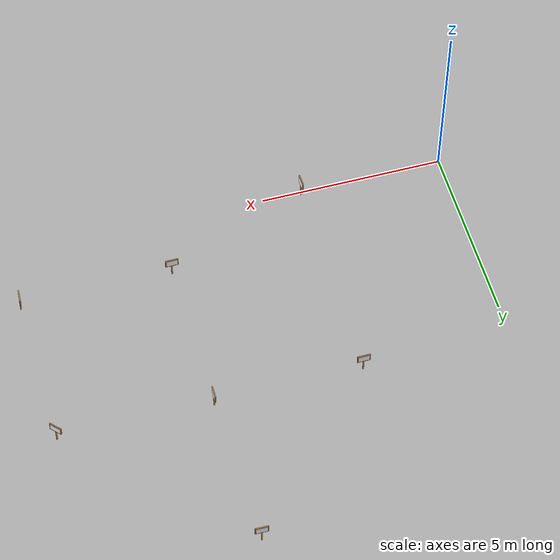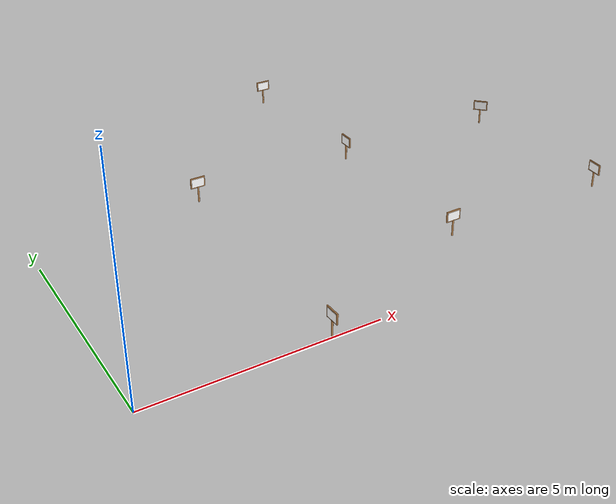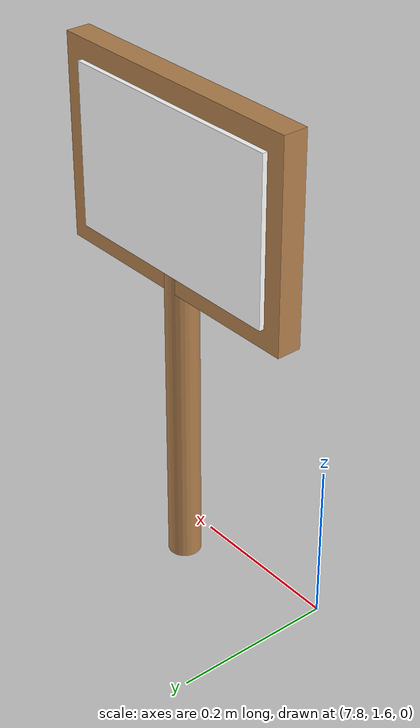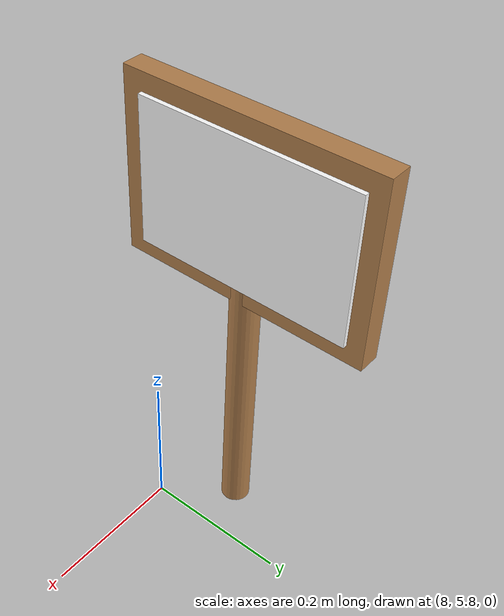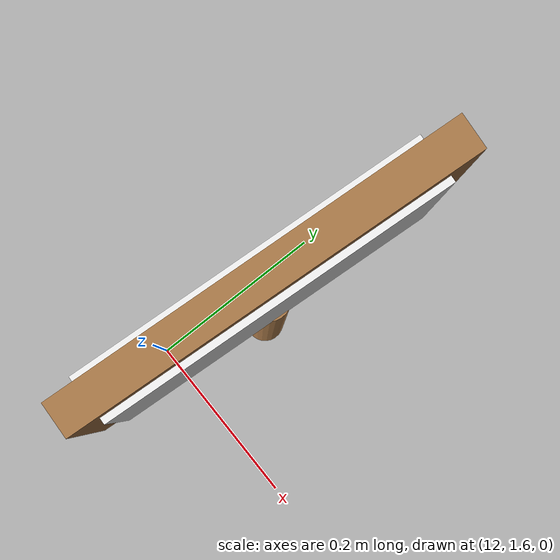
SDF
<sdf version="1.6">
 <world name="default">
  <light name="sun" type="directional">
   <pose>0 0 10 0 -0 0</pose>
   <diffuse>0.8 0.8 0.8 1</diffuse>
   <specular>0.2 0.2 0.2 1</specular>
   <attenuation>
    <range>1000</range>
    <constant>0.9</constant>
    <linear>0.01</linear>
    <quadratic>0.001</quadratic>
   </attenuation>
   <direction>-0.5 0.1 -0.9</direction>
  </light>
  <gravity>0 0 -9.8</gravity>
  <magnetic_field>6e-06 2.3e-05 -4.2e-05</magnetic_field>
  <atmosphere type="adiabatic"/>
  <physics name="default_physics" default="0" type="ode">
   <max_step_size>0.001</max_step_size>
   <real_time_factor>1</real_time_factor>
   <real_time_update_rate>1000</real_time_update_rate>
  </physics>
  <scene><ambient>0.4 0.4 0.4 1</ambient><background>0.7 0.7 0.7 1</background><shadows>1</shadows></scene>
  <audio><device>default</device></audio>
  <spherical_coordinates>
   <surface_model>EARTH_WGS84</surface_model>
   <latitude_deg>0</latitude_deg>
   <longitude_deg>0</longitude_deg>
   <elevation>0</elevation>
   <heading_deg>0</heading_deg>
  </spherical_coordinates>
  <model name="arrow_wood_thin">
   <link name="link_0">
    <inertial>
     <mass>1</mass>
     <inertia><ixx>0.145833</ixx><ixy>0</ixy><ixz>0</ixz><iyy>0.145833</iyy><iyz>0</iyz><izz>0.125</izz></inertia>
    </inertial>
    <pose>-0.017932 0.660168 -0.097628 0 -0 0</pose>
    <visual name="visual">
     <geometry><cylinder><radius>0.02</radius><length>0.4</length></cylinder></geometry>
     <material>
      <lighting>1</lighting>
      <script><uri>file://media/materials/scripts/gazebo.material</uri><name>Gazebo/Wood</name></script>
      <shader type="vertex"><normal_map>__default__</normal_map></shader>
      <ambient>0.3 0.3 0.3 1</ambient>
      <diffuse>0.7 0.7 0.7 1</diffuse>
      <specular>0.01 0.01 0.01 1</specular>
      <emissive>0 0 0 1</emissive>
     </material>
    </visual>
    <collision name="collision">
     <geometry><cylinder><radius>0.02</radius><length>0.4</length></cylinder></geometry>
     <surface>
      <friction>
       <ode><mu>1</mu><mu2>1</mu2><fdir1>0 0 0</fdir1><slip1>0</slip1><slip2>0</slip2></ode>
       <torsional>
        <coefficient>1</coefficient>
        <patch_radius>0</patch_radius>
        <surface_radius>0</surface_radius>
        <use_patch_radius>1</use_patch_radius>
        <ode><slip>0</slip></ode>
       </torsional>
      </friction>
      <bounce><restitution_coefficient>0</restitution_coefficient><threshold>1e+06</threshold></bounce>
      <contact>
       <collide_without_contact>0</collide_without_contact>
       <collide_without_contact_bitmask>1</collide_without_contact_bitmask>
       <collide_bitmask>1</collide_bitmask>
       <ode>
        <soft_cfm>0</soft_cfm>
        <soft_erp>0.2</soft_erp>
        <kp>1e+13</kp>
        <kd>1</kd>
        <max_vel>0.01</max_vel>
        <min_depth>0</min_depth>
       </ode>
       <bullet>
        <split_impulse>1</split_impulse>
        <split_impulse_penetration_threshold>-0.01</split_impulse_penetration_threshold>
        <soft_cfm>0</soft_cfm>
        <soft_erp>0.2</soft_erp>
        <kp>1e+13</kp>
        <kd>1</kd>
       </bullet>
      </contact>
     </surface>
    </collision>
   </link>
   <link name="link_1">
    <inertial>
     <mass>2.44097</mass>
     <inertia>
      <ixx>0.0264439</ixx>
      <ixy>0</ixy>
      <ixz>0</ixz>
      <iyy>0.0111671</iyy>
      <iyz>0</iyz>
      <izz>0.0213378</izz>
     </inertia>
    </inertial>
    <pose>-0.025899 0.66382 0.194379 0 -0 0</pose>
    <visual name="visual">
     <geometry><box><size>0.02 0.3 0.2</size></box></geometry>
     <material>
      <script><uri>file://scripts</uri><uri>file://textures</uri><name>arrow/standard</name></script>
      <emissive>0 0 0 1</emissive>
      <shader type="vertex"><normal_map>__default__</normal_map></shader>
      <ambient>1 1 1 1</ambient>
      <diffuse>1 1 1 1</diffuse>
      <specular>0 0 0 1</specular>
     </material>
    </visual>
    <collision name="collision">
     <geometry><box><size>0.02 0.3 0.2</size></box></geometry>
     <surface>
      <friction>
       <ode><mu>1</mu><mu2>1</mu2><fdir1>0 0 0</fdir1><slip1>0</slip1><slip2>0</slip2></ode>
       <torsional>
        <coefficient>1</coefficient>
        <patch_radius>0</patch_radius>
        <surface_radius>0</surface_radius>
        <use_patch_radius>1</use_patch_radius>
        <ode><slip>0</slip></ode>
       </torsional>
      </friction>
      <bounce><restitution_coefficient>0</restitution_coefficient><threshold>1e+06</threshold></bounce>
      <contact>
       <collide_without_contact>0</collide_without_contact>
       <collide_without_contact_bitmask>1</collide_without_contact_bitmask>
       <collide_bitmask>1</collide_bitmask>
       <ode>
        <soft_cfm>0</soft_cfm>
        <soft_erp>0.2</soft_erp>
        <kp>1e+13</kp>
        <kd>1</kd>
        <max_vel>0.01</max_vel>
        <min_depth>0</min_depth>
       </ode>
       <bullet>
        <split_impulse>1</split_impulse>
        <split_impulse_penetration_threshold>-0.01</split_impulse_penetration_threshold>
        <soft_cfm>0</soft_cfm>
        <soft_erp>0.2</soft_erp>
        <kp>1e+13</kp>
        <kd>1</kd>
       </bullet>
      </contact>
     </surface>
    </collision>
   </link>
   <link name="link_1_clone">
    <inertial>
     <mass>1</mass>
     <inertia>
      <ixx>0.166667</ixx>
      <ixy>0</ixy>
      <ixz>0</ixz>
      <iyy>0.166667</iyy>
      <iyz>0</iyz>
      <izz>0.166667</izz>
     </inertia>
    </inertial>
    <pose>-0.015207 0.663184 0.195267 0 -0 0</pose>
    <visual name="visual">
     <geometry><box><size>0.03 0.35 0.25</size></box></geometry>
     <material>
      <script><uri>file://scripts</uri><uri>file://textures</uri><name>Gazebo/Wood</name></script>
      <shader type="vertex"><normal_map>__default__</normal_map></shader>
      <ambient>1 1 1 1</ambient>
      <diffuse>1 1 1 1</diffuse>
      <specular>0 0 0 1</specular>
      <emissive>0 0 0 1</emissive>
     </material>
    </visual>
    <collision name="collision">
     <geometry><box><size>0.03 0.35 0.25</size></box></geometry>
     <surface>
      <friction>
       <ode><mu>1</mu><mu2>1</mu2><fdir1>0 0 0</fdir1><slip1>0</slip1><slip2>0</slip2></ode>
       <torsional>
        <coefficient>1</coefficient>
        <patch_radius>0</patch_radius>
        <surface_radius>0</surface_radius>
        <use_patch_radius>1</use_patch_radius>
        <ode><slip>0</slip></ode>
       </torsional>
      </friction>
      <bounce><restitution_coefficient>0</restitution_coefficient><threshold>1e+06</threshold></bounce>
      <contact>
       <collide_without_contact>0</collide_without_contact>
       <collide_without_contact_bitmask>1</collide_without_contact_bitmask>
       <collide_bitmask>1</collide_bitmask>
       <ode>
        <soft_cfm>0</soft_cfm>
        <soft_erp>0.2</soft_erp>
        <kp>1e+13</kp>
        <kd>1</kd>
        <max_vel>0.01</max_vel>
        <min_depth>0</min_depth>
       </ode>
       <bullet>
        <split_impulse>1</split_impulse>
        <split_impulse_penetration_threshold>-0.01</split_impulse_penetration_threshold>
        <soft_cfm>0</soft_cfm>
        <soft_erp>0.2</soft_erp>
        <kp>1e+13</kp>
        <kd>1</kd>
       </bullet>
      </contact>
     </surface>
    </collision>
   </link>
   <link name="link_1_clone_0">
    <inertial>
     <mass>0.516012</mass>
     <inertia>
      <ixx>0.00559013</ixx>
      <ixy>0</ixy>
      <ixz>0</ixz>
      <iyy>0.00174866</iyy>
      <iyz>0</iyz>
      <izz>0.00389871</izz>
     </inertia>
    </inertial>
    <pose>-0.00403 0.665261 0.195247 0 -0 0</pose>
    <visual name="visual">
     <geometry><box><size>0.02 0.3 0.2</size></box></geometry>
     <material>
      <script><uri>file://scripts</uri><uri>file://textures</uri><name>arrow/standard_opp</name></script>
      <emissive>0 0 0 1</emissive>
      <shader type="vertex"><normal_map>__default__</normal_map></shader>
      <ambient>1 1 1 1</ambient>
      <diffuse>1 1 1 1</diffuse>
      <specular>0 0 0 1</specular>
     </material>
    </visual>
    <collision name="collision">
     <geometry><box><size>0.02 0.3 0.2</size></box></geometry>
     <surface>
      <friction>
       <ode><mu>1</mu><mu2>1</mu2><fdir1>0 0 0</fdir1><slip1>0</slip1><slip2>0</slip2></ode>
       <torsional>
        <coefficient>1</coefficient>
        <patch_radius>0</patch_radius>
        <surface_radius>0</surface_radius>
        <use_patch_radius>1</use_patch_radius>
        <ode><slip>0</slip></ode>
       </torsional>
      </friction>
      <bounce><restitution_coefficient>0</restitution_coefficient><threshold>1e+06</threshold></bounce>
      <contact>
       <collide_without_contact>0</collide_without_contact>
       <collide_without_contact_bitmask>1</collide_without_contact_bitmask>
       <collide_bitmask>1</collide_bitmask>
       <ode>
        <soft_cfm>0</soft_cfm>
        <soft_erp>0.2</soft_erp>
        <kp>1e+13</kp>
        <kd>1</kd>
        <max_vel>0.01</max_vel>
        <min_depth>0</min_depth>
       </ode>
       <bullet>
        <split_impulse>1</split_impulse>
        <split_impulse_penetration_threshold>-0.01</split_impulse_penetration_threshold>
        <soft_cfm>0</soft_cfm>
        <soft_erp>0.2</soft_erp>
        <kp>1e+13</kp>
        <kd>1</kd>
       </bullet>
      </contact>
     </surface>
    </collision>
   </link>
   <joint name="link_0_JOINT_0" type="fixed">
    <parent>link_0</parent>
    <child>link_1</child>
    <physics>
     <ode><limit><cfm>0</cfm><erp>0.2</erp></limit><suspension><cfm>0</cfm><erp>0.2</erp></suspension></ode>
    </physics>
   </joint>
   <joint name="link_1_JOINT_0_0" type="fixed">
    <parent>link_1</parent>
    <child>link_1_clone_0</child>
    <physics>
     <ode><limit><cfm>0</cfm><erp>0.2</erp></limit><suspension><cfm>0</cfm><erp>0.2</erp></suspension></ode>
    </physics>
   </joint>
   <joint name="link_1_JOINT_0" type="fixed">
    <parent>link_1</parent>
    <child>link_1_clone</child>
    <physics>
     <ode><limit><cfm>0</cfm><erp>0.2</erp></limit><suspension><cfm>0</cfm><erp>0.2</erp></suspension></ode>
    </physics>
   </joint>
   <static>0</static>
   <pose>3.90153 0.701423 0.297258 -0.009093 0.002956 -3.10908</pose>
  </model>
  <model name="arrow_maze1">
   <model name="arrow_wood_thin">
    <link name="link_0">
     <inertial>
      <mass>1</mass>
      <inertia><ixx>0.145833</ixx><ixy>0</ixy><ixz>0</ixz><iyy>0.145833</iyy><iyz>0</iyz><izz>0.125</izz></inertia>
     </inertial>
     <pose>-0.017932 0.660168 -0.097628 0 -0 0</pose>
     <visual name="visual">
      <geometry><cylinder><radius>0.02</radius><length>0.4</length></cylinder></geometry>
      <material>
       <lighting>1</lighting>
       <script><uri>file://media/materials/scripts/gazebo.material</uri><name>Gazebo/Wood</name></script>
       <shader type="vertex"><normal_map>__default__</normal_map></shader>
       <ambient>0.3 0.3 0.3 1</ambient>
       <diffuse>0.7 0.7 0.7 1</diffuse>
       <specular>0.01 0.01 0.01 1</specular>
       <emissive>0 0 0 1</emissive>
      </material>
     </visual>
     <collision name="collision">
      <geometry><cylinder><radius>0.02</radius><length>0.4</length></cylinder></geometry>
      <surface>
       <friction>
        <ode><mu>1</mu><mu2>1</mu2><fdir1>0 0 0</fdir1><slip1>0</slip1><slip2>0</slip2></ode>
        <torsional>
         <coefficient>1</coefficient>
         <patch_radius>0</patch_radius>
         <surface_radius>0</surface_radius>
         <use_patch_radius>1</use_patch_radius>
         <ode><slip>0</slip></ode>
        </torsional>
       </friction>
       <bounce><restitution_coefficient>0</restitution_coefficient><threshold>1e+06</threshold></bounce>
       <contact>
        <collide_without_contact>0</collide_without_contact>
        <collide_without_contact_bitmask>1</collide_without_contact_bitmask>
        <collide_bitmask>1</collide_bitmask>
        <ode>
         <soft_cfm>0</soft_cfm>
         <soft_erp>0.2</soft_erp>
         <kp>1e+13</kp>
         <kd>1</kd>
         <max_vel>0.01</max_vel>
         <min_depth>0</min_depth>
        </ode>
        <bullet>
         <split_impulse>1</split_impulse>
         <split_impulse_penetration_threshold>-0.01</split_impulse_penetration_threshold>
         <soft_cfm>0</soft_cfm>
         <soft_erp>0.2</soft_erp>
         <kp>1e+13</kp>
         <kd>1</kd>
        </bullet>
       </contact>
      </surface>
     </collision>
    </link>
    <link name="link_1">
     <inertial>
      <mass>2.44097</mass>
      <inertia>
       <ixx>0.0264439</ixx>
       <ixy>0</ixy>
       <ixz>0</ixz>
       <iyy>0.0111671</iyy>
       <iyz>0</iyz>
       <izz>0.0213378</izz>
      </inertia>
     </inertial>
     <pose>-0.025899 0.66382 0.194379 0 -0 0</pose>
     <visual name="visual">
      <geometry><box><size>0.02 0.3 0.2</size></box></geometry>
      <material>
       <script><uri>file://scripts</uri><uri>file://textures</uri><name>arrow/standard</name></script>
       <emissive>0 0 0 1</emissive>
       <shader type="vertex"><normal_map>__default__</normal_map></shader>
       <ambient>1 1 1 1</ambient>
       <diffuse>1 1 1 1</diffuse>
       <specular>0 0 0 1</specular>
      </material>
     </visual>
     <collision name="collision">
      <geometry><box><size>0.02 0.3 0.2</size></box></geometry>
      <surface>
       <friction>
        <ode><mu>1</mu><mu2>1</mu2><fdir1>0 0 0</fdir1><slip1>0</slip1><slip2>0</slip2></ode>
        <torsional>
         <coefficient>1</coefficient>
         <patch_radius>0</patch_radius>
         <surface_radius>0</surface_radius>
         <use_patch_radius>1</use_patch_radius>
         <ode><slip>0</slip></ode>
        </torsional>
       </friction>
       <bounce><restitution_coefficient>0</restitution_coefficient><threshold>1e+06</threshold></bounce>
       <contact>
        <collide_without_contact>0</collide_without_contact>
        <collide_without_contact_bitmask>1</collide_without_contact_bitmask>
        <collide_bitmask>1</collide_bitmask>
        <ode>
         <soft_cfm>0</soft_cfm>
         <soft_erp>0.2</soft_erp>
         <kp>1e+13</kp>
         <kd>1</kd>
         <max_vel>0.01</max_vel>
         <min_depth>0</min_depth>
        </ode>
        <bullet>
         <split_impulse>1</split_impulse>
         <split_impulse_penetration_threshold>-0.01</split_impulse_penetration_threshold>
         <soft_cfm>0</soft_cfm>
         <soft_erp>0.2</soft_erp>
         <kp>1e+13</kp>
         <kd>1</kd>
        </bullet>
       </contact>
      </surface>
     </collision>
    </link>
    <link name="link_1_clone">
     <inertial>
      <mass>1</mass>
      <inertia>
       <ixx>0.166667</ixx>
       <ixy>0</ixy>
       <ixz>0</ixz>
       <iyy>0.166667</iyy>
       <iyz>0</iyz>
       <izz>0.166667</izz>
      </inertia>
     </inertial>
     <pose>-0.015207 0.663184 0.195267 0 -0 0</pose>
     <visual name="visual">
      <geometry><box><size>0.03 0.35 0.25</size></box></geometry>
      <material>
       <script><uri>file://scripts</uri><uri>file://textures</uri><name>Gazebo/Wood</name></script>
       <shader type="vertex"><normal_map>__default__</normal_map></shader>
       <ambient>1 1 1 1</ambient>
       <diffuse>1 1 1 1</diffuse>
       <specular>0 0 0 1</specular>
       <emissive>0 0 0 1</emissive>
      </material>
     </visual>
     <collision name="collision">
      <geometry><box><size>0.03 0.35 0.25</size></box></geometry>
      <surface>
       <friction>
        <ode><mu>1</mu><mu2>1</mu2><fdir1>0 0 0</fdir1><slip1>0</slip1><slip2>0</slip2></ode>
        <torsional>
         <coefficient>1</coefficient>
         <patch_radius>0</patch_radius>
         <surface_radius>0</surface_radius>
         <use_patch_radius>1</use_patch_radius>
         <ode><slip>0</slip></ode>
        </torsional>
       </friction>
       <bounce><restitution_coefficient>0</restitution_coefficient><threshold>1e+06</threshold></bounce>
       <contact>
        <collide_without_contact>0</collide_without_contact>
        <collide_without_contact_bitmask>1</collide_without_contact_bitmask>
        <collide_bitmask>1</collide_bitmask>
        <ode>
         <soft_cfm>0</soft_cfm>
         <soft_erp>0.2</soft_erp>
         <kp>1e+13</kp>
         <kd>1</kd>
         <max_vel>0.01</max_vel>
         <min_depth>0</min_depth>
        </ode>
        <bullet>
         <split_impulse>1</split_impulse>
         <split_impulse_penetration_threshold>-0.01</split_impulse_penetration_threshold>
         <soft_cfm>0</soft_cfm>
         <soft_erp>0.2</soft_erp>
         <kp>1e+13</kp>
         <kd>1</kd>
        </bullet>
       </contact>
      </surface>
     </collision>
    </link>
    <link name="link_1_clone_0">
     <inertial>
      <mass>0.516012</mass>
      <inertia>
       <ixx>0.00559013</ixx>
       <ixy>0</ixy>
       <ixz>0</ixz>
       <iyy>0.00174866</iyy>
       <iyz>0</iyz>
       <izz>0.00389871</izz>
      </inertia>
     </inertial>
     <pose>-0.00403 0.665261 0.195247 0 -0 0</pose>
     <visual name="visual">
      <geometry><box><size>0.02 0.3 0.2</size></box></geometry>
      <material>
       <script><uri>file://scripts</uri><uri>file://textures</uri><name>arrow/standard_opp</name></script>
       <emissive>0 0 0 1</emissive>
       <shader type="vertex"><normal_map>__default__</normal_map></shader>
       <ambient>1 1 1 1</ambient>
       <diffuse>1 1 1 1</diffuse>
       <specular>0 0 0 1</specular>
      </material>
     </visual>
     <collision name="collision">
      <geometry><box><size>0.02 0.3 0.2</size></box></geometry>
      <surface>
       <friction>
        <ode><mu>1</mu><mu2>1</mu2><fdir1>0 0 0</fdir1><slip1>0</slip1><slip2>0</slip2></ode>
        <torsional>
         <coefficient>1</coefficient>
         <patch_radius>0</patch_radius>
         <surface_radius>0</surface_radius>
         <use_patch_radius>1</use_patch_radius>
         <ode><slip>0</slip></ode>
        </torsional>
       </friction>
       <bounce><restitution_coefficient>0</restitution_coefficient><threshold>1e+06</threshold></bounce>
       <contact>
        <collide_without_contact>0</collide_without_contact>
        <collide_without_contact_bitmask>1</collide_without_contact_bitmask>
        <collide_bitmask>1</collide_bitmask>
        <ode>
         <soft_cfm>0</soft_cfm>
         <soft_erp>0.2</soft_erp>
         <kp>1e+13</kp>
         <kd>1</kd>
         <max_vel>0.01</max_vel>
         <min_depth>0</min_depth>
        </ode>
        <bullet>
         <split_impulse>1</split_impulse>
         <split_impulse_penetration_threshold>-0.01</split_impulse_penetration_threshold>
         <soft_cfm>0</soft_cfm>
         <soft_erp>0.2</soft_erp>
         <kp>1e+13</kp>
         <kd>1</kd>
        </bullet>
       </contact>
      </surface>
     </collision>
    </link>
    <joint name="link_0_JOINT_0" type="fixed">
     <parent>link_0</parent>
     <child>link_1</child>
     <physics>
      <ode><limit><cfm>0</cfm><erp>0.2</erp></limit><suspension><cfm>0</cfm><erp>0.2</erp></suspension></ode>
     </physics>
    </joint>
    <joint name="link_1_JOINT_0_0" type="fixed">
     <parent>link_1</parent>
     <child>link_1_clone_0</child>
     <physics>
      <ode><limit><cfm>0</cfm><erp>0.2</erp></limit><suspension><cfm>0</cfm><erp>0.2</erp></suspension></ode>
     </physics>
    </joint>
    <joint name="link_1_JOINT_0" type="fixed">
     <parent>link_1</parent>
     <child>link_1_clone</child>
     <physics>
      <ode><limit><cfm>0</cfm><erp>0.2</erp></limit><suspension><cfm>0</cfm><erp>0.2</erp></suspension></ode>
     </physics>
    </joint>
    <static>0</static>
    <pose>-4.38621 0.976128 0 0 -0 1.56944</pose>
   </model>
   <model name="arrow_wood_thin_0">
    <link name="link_0">
     <inertial>
      <mass>1</mass>
      <inertia><ixx>0.145833</ixx><ixy>0</ixy><ixz>0</ixz><iyy>0.145833</iyy><iyz>0</iyz><izz>0.125</izz></inertia>
     </inertial>
     <pose>-0.017932 0.660168 -0.097628 0 -0 0</pose>
     <visual name="visual">
      <geometry><cylinder><radius>0.02</radius><length>0.4</length></cylinder></geometry>
      <material>
       <lighting>1</lighting>
       <script><uri>file://media/materials/scripts/gazebo.material</uri><name>Gazebo/Wood</name></script>
       <shader type="vertex"><normal_map>__default__</normal_map></shader>
       <ambient>0.3 0.3 0.3 1</ambient>
       <diffuse>0.7 0.7 0.7 1</diffuse>
       <specular>0.01 0.01 0.01 1</specular>
       <emissive>0 0 0 1</emissive>
      </material>
     </visual>
     <collision name="collision">
      <geometry><cylinder><radius>0.02</radius><length>0.4</length></cylinder></geometry>
      <surface>
       <friction>
        <ode><mu>1</mu><mu2>1</mu2><fdir1>0 0 0</fdir1><slip1>0</slip1><slip2>0</slip2></ode>
        <torsional>
         <coefficient>1</coefficient>
         <patch_radius>0</patch_radius>
         <surface_radius>0</surface_radius>
         <use_patch_radius>1</use_patch_radius>
         <ode><slip>0</slip></ode>
        </torsional>
       </friction>
       <bounce><restitution_coefficient>0</restitution_coefficient><threshold>1e+06</threshold></bounce>
       <contact>
        <collide_without_contact>0</collide_without_contact>
        <collide_without_contact_bitmask>1</collide_without_contact_bitmask>
        <collide_bitmask>1</collide_bitmask>
        <ode>
         <soft_cfm>0</soft_cfm>
         <soft_erp>0.2</soft_erp>
         <kp>1e+13</kp>
         <kd>1</kd>
         <max_vel>0.01</max_vel>
         <min_depth>0</min_depth>
        </ode>
        <bullet>
         <split_impulse>1</split_impulse>
         <split_impulse_penetration_threshold>-0.01</split_impulse_penetration_threshold>
         <soft_cfm>0</soft_cfm>
         <soft_erp>0.2</soft_erp>
         <kp>1e+13</kp>
         <kd>1</kd>
        </bullet>
       </contact>
      </surface>
     </collision>
    </link>
    <link name="link_1">
     <inertial>
      <mass>2.44097</mass>
      <inertia>
       <ixx>0.0264439</ixx>
       <ixy>0</ixy>
       <ixz>0</ixz>
       <iyy>0.0111671</iyy>
       <iyz>0</iyz>
       <izz>0.0213378</izz>
      </inertia>
     </inertial>
     <pose>-0.025899 0.66382 0.194379 0 -0 0</pose>
     <visual name="visual">
      <geometry><box><size>0.02 0.3 0.2</size></box></geometry>
      <material>
       <script><uri>file://scripts</uri><uri>file://textures</uri><name>arrow/standard</name></script>
       <emissive>0 0 0 1</emissive>
       <shader type="vertex"><normal_map>__default__</normal_map></shader>
       <ambient>1 1 1 1</ambient>
       <diffuse>1 1 1 1</diffuse>
       <specular>0 0 0 1</specular>
      </material>
     </visual>
     <collision name="collision">
      <geometry><box><size>0.02 0.3 0.2</size></box></geometry>
      <surface>
       <friction>
        <ode><mu>1</mu><mu2>1</mu2><fdir1>0 0 0</fdir1><slip1>0</slip1><slip2>0</slip2></ode>
        <torsional>
         <coefficient>1</coefficient>
         <patch_radius>0</patch_radius>
         <surface_radius>0</surface_radius>
         <use_patch_radius>1</use_patch_radius>
         <ode><slip>0</slip></ode>
        </torsional>
       </friction>
       <bounce><restitution_coefficient>0</restitution_coefficient><threshold>1e+06</threshold></bounce>
       <contact>
        <collide_without_contact>0</collide_without_contact>
        <collide_without_contact_bitmask>1</collide_without_contact_bitmask>
        <collide_bitmask>1</collide_bitmask>
        <ode>
         <soft_cfm>0</soft_cfm>
         <soft_erp>0.2</soft_erp>
         <kp>1e+13</kp>
         <kd>1</kd>
         <max_vel>0.01</max_vel>
         <min_depth>0</min_depth>
        </ode>
        <bullet>
         <split_impulse>1</split_impulse>
         <split_impulse_penetration_threshold>-0.01</split_impulse_penetration_threshold>
         <soft_cfm>0</soft_cfm>
         <soft_erp>0.2</soft_erp>
         <kp>1e+13</kp>
         <kd>1</kd>
        </bullet>
       </contact>
      </surface>
     </collision>
    </link>
    <link name="link_1_clone">
     <inertial>
      <mass>1</mass>
      <inertia>
       <ixx>0.166667</ixx>
       <ixy>0</ixy>
       <ixz>0</ixz>
       <iyy>0.166667</iyy>
       <iyz>0</iyz>
       <izz>0.166667</izz>
      </inertia>
     </inertial>
     <pose>-0.015207 0.663184 0.195267 0 -0 0</pose>
     <visual name="visual">
      <geometry><box><size>0.03 0.35 0.25</size></box></geometry>
      <material>
       <script><uri>file://scripts</uri><uri>file://textures</uri><name>Gazebo/Wood</name></script>
       <shader type="vertex"><normal_map>__default__</normal_map></shader>
       <ambient>1 1 1 1</ambient>
       <diffuse>1 1 1 1</diffuse>
       <specular>0 0 0 1</specular>
       <emissive>0 0 0 1</emissive>
      </material>
     </visual>
     <collision name="collision">
      <geometry><box><size>0.03 0.35 0.25</size></box></geometry>
      <surface>
       <friction>
        <ode><mu>1</mu><mu2>1</mu2><fdir1>0 0 0</fdir1><slip1>0</slip1><slip2>0</slip2></ode>
        <torsional>
         <coefficient>1</coefficient>
         <patch_radius>0</patch_radius>
         <surface_radius>0</surface_radius>
         <use_patch_radius>1</use_patch_radius>
         <ode><slip>0</slip></ode>
        </torsional>
       </friction>
       <bounce><restitution_coefficient>0</restitution_coefficient><threshold>1e+06</threshold></bounce>
       <contact>
        <collide_without_contact>0</collide_without_contact>
        <collide_without_contact_bitmask>1</collide_without_contact_bitmask>
        <collide_bitmask>1</collide_bitmask>
        <ode>
         <soft_cfm>0</soft_cfm>
         <soft_erp>0.2</soft_erp>
         <kp>1e+13</kp>
         <kd>1</kd>
         <max_vel>0.01</max_vel>
         <min_depth>0</min_depth>
        </ode>
        <bullet>
         <split_impulse>1</split_impulse>
         <split_impulse_penetration_threshold>-0.01</split_impulse_penetration_threshold>
         <soft_cfm>0</soft_cfm>
         <soft_erp>0.2</soft_erp>
         <kp>1e+13</kp>
         <kd>1</kd>
        </bullet>
       </contact>
      </surface>
     </collision>
    </link>
    <link name="link_1_clone_0">
     <inertial>
      <mass>0.516012</mass>
      <inertia>
       <ixx>0.00559013</ixx>
       <ixy>0</ixy>
       <ixz>0</ixz>
       <iyy>0.00174866</iyy>
       <iyz>0</iyz>
       <izz>0.00389871</izz>
      </inertia>
     </inertial>
     <pose>-0.00403 0.665261 0.195247 0 -0 0</pose>
     <visual name="visual">
      <geometry><box><size>0.02 0.3 0.2</size></box></geometry>
      <material>
       <script><uri>file://scripts</uri><uri>file://textures</uri><name>arrow/standard_opp</name></script>
       <emissive>0 0 0 1</emissive>
       <shader type="vertex"><normal_map>__default__</normal_map></shader>
       <ambient>1 1 1 1</ambient>
       <diffuse>1 1 1 1</diffuse>
       <specular>0 0 0 1</specular>
      </material>
     </visual>
     <collision name="collision">
      <geometry><box><size>0.02 0.3 0.2</size></box></geometry>
      <surface>
       <friction>
        <ode><mu>1</mu><mu2>1</mu2><fdir1>0 0 0</fdir1><slip1>0</slip1><slip2>0</slip2></ode>
        <torsional>
         <coefficient>1</coefficient>
         <patch_radius>0</patch_radius>
         <surface_radius>0</surface_radius>
         <use_patch_radius>1</use_patch_radius>
         <ode><slip>0</slip></ode>
        </torsional>
       </friction>
       <bounce><restitution_coefficient>0</restitution_coefficient><threshold>1e+06</threshold></bounce>
       <contact>
        <collide_without_contact>0</collide_without_contact>
        <collide_without_contact_bitmask>1</collide_without_contact_bitmask>
        <collide_bitmask>1</collide_bitmask>
        <ode>
         <soft_cfm>0</soft_cfm>
         <soft_erp>0.2</soft_erp>
         <kp>1e+13</kp>
         <kd>1</kd>
         <max_vel>0.01</max_vel>
         <min_depth>0</min_depth>
        </ode>
        <bullet>
         <split_impulse>1</split_impulse>
         <split_impulse_penetration_threshold>-0.01</split_impulse_penetration_threshold>
         <soft_cfm>0</soft_cfm>
         <soft_erp>0.2</soft_erp>
         <kp>1e+13</kp>
         <kd>1</kd>
        </bullet>
       </contact>
      </surface>
     </collision>
    </link>
    <joint name="link_0_JOINT_0" type="fixed">
     <parent>link_0</parent>
     <child>link_1</child>
     <physics>
      <ode><limit><cfm>0</cfm><erp>0.2</erp></limit><suspension><cfm>0</cfm><erp>0.2</erp></suspension></ode>
     </physics>
    </joint>
    <joint name="link_1_JOINT_0_0" type="fixed">
     <parent>link_1</parent>
     <child>link_1_clone_0</child>
     <physics>
      <ode><limit><cfm>0</cfm><erp>0.2</erp></limit><suspension><cfm>0</cfm><erp>0.2</erp></suspension></ode>
     </physics>
    </joint>
    <joint name="link_1_JOINT_0" type="fixed">
     <parent>link_1</parent>
     <child>link_1_clone</child>
     <physics>
      <ode><limit><cfm>0</cfm><erp>0.2</erp></limit><suspension><cfm>0</cfm><erp>0.2</erp></suspension></ode>
     </physics>
    </joint>
    <static>0</static>
    <pose>-1.0729 0.322933 -0 0 -0 0</pose>
   </model>
   <model name="arrow_wood_thin_1">
    <link name="link_0">
     <inertial>
      <mass>1</mass>
      <inertia><ixx>0.145833</ixx><ixy>0</ixy><ixz>0</ixz><iyy>0.145833</iyy><iyz>0</iyz><izz>0.125</izz></inertia>
     </inertial>
     <pose>-0.017932 0.660168 -0.097628 0 -0 0</pose>
     <visual name="visual">
      <geometry><cylinder><radius>0.02</radius><length>0.4</length></cylinder></geometry>
      <material>
       <lighting>1</lighting>
       <script><uri>file://media/materials/scripts/gazebo.material</uri><name>Gazebo/Wood</name></script>
       <shader type="vertex"><normal_map>__default__</normal_map></shader>
       <ambient>0.3 0.3 0.3 1</ambient>
       <diffuse>0.7 0.7 0.7 1</diffuse>
       <specular>0.01 0.01 0.01 1</specular>
       <emissive>0 0 0 1</emissive>
      </material>
     </visual>
     <collision name="collision">
      <geometry><cylinder><radius>0.02</radius><length>0.4</length></cylinder></geometry>
      <surface>
       <friction>
        <ode><mu>1</mu><mu2>1</mu2><fdir1>0 0 0</fdir1><slip1>0</slip1><slip2>0</slip2></ode>
        <torsional>
         <coefficient>1</coefficient>
         <patch_radius>0</patch_radius>
         <surface_radius>0</surface_radius>
         <use_patch_radius>1</use_patch_radius>
         <ode><slip>0</slip></ode>
        </torsional>
       </friction>
       <bounce><restitution_coefficient>0</restitution_coefficient><threshold>1e+06</threshold></bounce>
       <contact>
        <collide_without_contact>0</collide_without_contact>
        <collide_without_contact_bitmask>1</collide_without_contact_bitmask>
        <collide_bitmask>1</collide_bitmask>
        <ode>
         <soft_cfm>0</soft_cfm>
         <soft_erp>0.2</soft_erp>
         <kp>1e+13</kp>
         <kd>1</kd>
         <max_vel>0.01</max_vel>
         <min_depth>0</min_depth>
        </ode>
        <bullet>
         <split_impulse>1</split_impulse>
         <split_impulse_penetration_threshold>-0.01</split_impulse_penetration_threshold>
         <soft_cfm>0</soft_cfm>
         <soft_erp>0.2</soft_erp>
         <kp>1e+13</kp>
         <kd>1</kd>
        </bullet>
       </contact>
      </surface>
     </collision>
    </link>
    <link name="link_1">
     <inertial>
      <mass>2.44097</mass>
      <inertia>
       <ixx>0.0264439</ixx>
       <ixy>0</ixy>
       <ixz>0</ixz>
       <iyy>0.0111671</iyy>
       <iyz>0</iyz>
       <izz>0.0213378</izz>
      </inertia>
     </inertial>
     <pose>-0.025899 0.66382 0.194379 0 -0 0</pose>
     <visual name="visual">
      <geometry><box><size>0.02 0.3 0.2</size></box></geometry>
      <material>
       <script><uri>file://scripts</uri><uri>file://textures</uri><name>arrow/standard</name></script>
       <emissive>0 0 0 1</emissive>
       <shader type="vertex"><normal_map>__default__</normal_map></shader>
       <ambient>1 1 1 1</ambient>
       <diffuse>1 1 1 1</diffuse>
       <specular>0 0 0 1</specular>
      </material>
     </visual>
     <collision name="collision">
      <geometry><box><size>0.02 0.3 0.2</size></box></geometry>
      <surface>
       <friction>
        <ode><mu>1</mu><mu2>1</mu2><fdir1>0 0 0</fdir1><slip1>0</slip1><slip2>0</slip2></ode>
        <torsional>
         <coefficient>1</coefficient>
         <patch_radius>0</patch_radius>
         <surface_radius>0</surface_radius>
         <use_patch_radius>1</use_patch_radius>
         <ode><slip>0</slip></ode>
        </torsional>
       </friction>
       <bounce><restitution_coefficient>0</restitution_coefficient><threshold>1e+06</threshold></bounce>
       <contact>
        <collide_without_contact>0</collide_without_contact>
        <collide_without_contact_bitmask>1</collide_without_contact_bitmask>
        <collide_bitmask>1</collide_bitmask>
        <ode>
         <soft_cfm>0</soft_cfm>
         <soft_erp>0.2</soft_erp>
         <kp>1e+13</kp>
         <kd>1</kd>
         <max_vel>0.01</max_vel>
         <min_depth>0</min_depth>
        </ode>
        <bullet>
         <split_impulse>1</split_impulse>
         <split_impulse_penetration_threshold>-0.01</split_impulse_penetration_threshold>
         <soft_cfm>0</soft_cfm>
         <soft_erp>0.2</soft_erp>
         <kp>1e+13</kp>
         <kd>1</kd>
        </bullet>
       </contact>
      </surface>
     </collision>
    </link>
    <link name="link_1_clone">
     <inertial>
      <mass>1</mass>
      <inertia>
       <ixx>0.166667</ixx>
       <ixy>0</ixy>
       <ixz>0</ixz>
       <iyy>0.166667</iyy>
       <iyz>0</iyz>
       <izz>0.166667</izz>
      </inertia>
     </inertial>
     <pose>-0.015207 0.663184 0.195267 0 -0 0</pose>
     <visual name="visual">
      <geometry><box><size>0.03 0.35 0.25</size></box></geometry>
      <material>
       <script><uri>file://scripts</uri><uri>file://textures</uri><name>Gazebo/Wood</name></script>
       <shader type="vertex"><normal_map>__default__</normal_map></shader>
       <ambient>1 1 1 1</ambient>
       <diffuse>1 1 1 1</diffuse>
       <specular>0 0 0 1</specular>
       <emissive>0 0 0 1</emissive>
      </material>
     </visual>
     <collision name="collision">
      <geometry><box><size>0.03 0.35 0.25</size></box></geometry>
      <surface>
       <friction>
        <ode><mu>1</mu><mu2>1</mu2><fdir1>0 0 0</fdir1><slip1>0</slip1><slip2>0</slip2></ode>
        <torsional>
         <coefficient>1</coefficient>
         <patch_radius>0</patch_radius>
         <surface_radius>0</surface_radius>
         <use_patch_radius>1</use_patch_radius>
         <ode><slip>0</slip></ode>
        </torsional>
       </friction>
       <bounce><restitution_coefficient>0</restitution_coefficient><threshold>1e+06</threshold></bounce>
       <contact>
        <collide_without_contact>0</collide_without_contact>
        <collide_without_contact_bitmask>1</collide_without_contact_bitmask>
        <collide_bitmask>1</collide_bitmask>
        <ode>
         <soft_cfm>0</soft_cfm>
         <soft_erp>0.2</soft_erp>
         <kp>1e+13</kp>
         <kd>1</kd>
         <max_vel>0.01</max_vel>
         <min_depth>0</min_depth>
        </ode>
        <bullet>
         <split_impulse>1</split_impulse>
         <split_impulse_penetration_threshold>-0.01</split_impulse_penetration_threshold>
         <soft_cfm>0</soft_cfm>
         <soft_erp>0.2</soft_erp>
         <kp>1e+13</kp>
         <kd>1</kd>
        </bullet>
       </contact>
      </surface>
     </collision>
    </link>
    <link name="link_1_clone_0">
     <inertial>
      <mass>0.516012</mass>
      <inertia>
       <ixx>0.00559013</ixx>
       <ixy>0</ixy>
       <ixz>0</ixz>
       <iyy>0.00174866</iyy>
       <iyz>0</iyz>
       <izz>0.00389871</izz>
      </inertia>
     </inertial>
     <pose>-0.00403 0.665261 0.195247 0 -0 0</pose>
     <visual name="visual">
      <geometry><box><size>0.02 0.3 0.2</size></box></geometry>
      <material>
       <script><uri>file://scripts</uri><uri>file://textures</uri><name>arrow/standard_opp</name></script>
       <emissive>0 0 0 1</emissive>
       <shader type="vertex"><normal_map>__default__</normal_map></shader>
       <ambient>1 1 1 1</ambient>
       <diffuse>1 1 1 1</diffuse>
       <specular>0 0 0 1</specular>
      </material>
     </visual>
     <collision name="collision">
      <geometry><box><size>0.02 0.3 0.2</size></box></geometry>
      <surface>
       <friction>
        <ode><mu>1</mu><mu2>1</mu2><fdir1>0 0 0</fdir1><slip1>0</slip1><slip2>0</slip2></ode>
        <torsional>
         <coefficient>1</coefficient>
         <patch_radius>0</patch_radius>
         <surface_radius>0</surface_radius>
         <use_patch_radius>1</use_patch_radius>
         <ode><slip>0</slip></ode>
        </torsional>
       </friction>
       <bounce><restitution_coefficient>0</restitution_coefficient><threshold>1e+06</threshold></bounce>
       <contact>
        <collide_without_contact>0</collide_without_contact>
        <collide_without_contact_bitmask>1</collide_without_contact_bitmask>
        <collide_bitmask>1</collide_bitmask>
        <ode>
         <soft_cfm>0</soft_cfm>
         <soft_erp>0.2</soft_erp>
         <kp>1e+13</kp>
         <kd>1</kd>
         <max_vel>0.01</max_vel>
         <min_depth>0</min_depth>
        </ode>
        <bullet>
         <split_impulse>1</split_impulse>
         <split_impulse_penetration_threshold>-0.01</split_impulse_penetration_threshold>
         <soft_cfm>0</soft_cfm>
         <soft_erp>0.2</soft_erp>
         <kp>1e+13</kp>
         <kd>1</kd>
        </bullet>
       </contact>
      </surface>
     </collision>
    </link>
    <joint name="link_0_JOINT_0" type="fixed">
     <parent>link_0</parent>
     <child>link_1</child>
     <physics>
      <ode><limit><cfm>0</cfm><erp>0.2</erp></limit><suspension><cfm>0</cfm><erp>0.2</erp></suspension></ode>
     </physics>
    </joint>
    <joint name="link_1_JOINT_0_0" type="fixed">
     <parent>link_1</parent>
     <child>link_1_clone_0</child>
     <physics>
      <ode><limit><cfm>0</cfm><erp>0.2</erp></limit><suspension><cfm>0</cfm><erp>0.2</erp></suspension></ode>
     </physics>
    </joint>
    <joint name="link_1_JOINT_0" type="fixed">
     <parent>link_1</parent>
     <child>link_1_clone</child>
     <physics>
      <ode><limit><cfm>0</cfm><erp>0.2</erp></limit><suspension><cfm>0</cfm><erp>0.2</erp></suspension></ode>
     </physics>
    </joint>
    <static>0</static>
    <pose>-0.398383 -3.20124 0 0 -0 1.58196</pose>
   </model>
   <model name="arrow_wood_thin_2">
    <link name="link_0">
     <inertial>
      <mass>1</mass>
      <inertia><ixx>0.145833</ixx><ixy>0</ixy><ixz>0</ixz><iyy>0.145833</iyy><iyz>0</iyz><izz>0.125</izz></inertia>
     </inertial>
     <pose>-0.017932 0.660168 -0.097628 0 -0 0</pose>
     <visual name="visual">
      <geometry><cylinder><radius>0.02</radius><length>0.4</length></cylinder></geometry>
      <material>
       <lighting>1</lighting>
       <script><uri>file://media/materials/scripts/gazebo.material</uri><name>Gazebo/Wood</name></script>
       <shader type="vertex"><normal_map>__default__</normal_map></shader>
       <ambient>0.3 0.3 0.3 1</ambient>
       <diffuse>0.7 0.7 0.7 1</diffuse>
       <specular>0.01 0.01 0.01 1</specular>
       <emissive>0 0 0 1</emissive>
      </material>
     </visual>
     <collision name="collision">
      <geometry><cylinder><radius>0.02</radius><length>0.4</length></cylinder></geometry>
      <surface>
       <friction>
        <ode><mu>1</mu><mu2>1</mu2><fdir1>0 0 0</fdir1><slip1>0</slip1><slip2>0</slip2></ode>
        <torsional>
         <coefficient>1</coefficient>
         <patch_radius>0</patch_radius>
         <surface_radius>0</surface_radius>
         <use_patch_radius>1</use_patch_radius>
         <ode><slip>0</slip></ode>
        </torsional>
       </friction>
       <bounce><restitution_coefficient>0</restitution_coefficient><threshold>1e+06</threshold></bounce>
       <contact>
        <collide_without_contact>0</collide_without_contact>
        <collide_without_contact_bitmask>1</collide_without_contact_bitmask>
        <collide_bitmask>1</collide_bitmask>
        <ode>
         <soft_cfm>0</soft_cfm>
         <soft_erp>0.2</soft_erp>
         <kp>1e+13</kp>
         <kd>1</kd>
         <max_vel>0.01</max_vel>
         <min_depth>0</min_depth>
        </ode>
        <bullet>
         <split_impulse>1</split_impulse>
         <split_impulse_penetration_threshold>-0.01</split_impulse_penetration_threshold>
         <soft_cfm>0</soft_cfm>
         <soft_erp>0.2</soft_erp>
         <kp>1e+13</kp>
         <kd>1</kd>
        </bullet>
       </contact>
      </surface>
     </collision>
    </link>
    <link name="link_1">
     <inertial>
      <mass>2.44097</mass>
      <inertia>
       <ixx>0.0264439</ixx>
       <ixy>0</ixy>
       <ixz>0</ixz>
       <iyy>0.0111671</iyy>
       <iyz>0</iyz>
       <izz>0.0213378</izz>
      </inertia>
     </inertial>
     <pose>-0.025899 0.66382 0.194379 0 -0 0</pose>
     <visual name="visual">
      <geometry><box><size>0.02 0.3 0.2</size></box></geometry>
      <material>
       <script><uri>file://scripts</uri><uri>file://textures</uri><name>arrow/standard</name></script>
       <emissive>0 0 0 1</emissive>
       <shader type="vertex"><normal_map>__default__</normal_map></shader>
       <ambient>1 1 1 1</ambient>
       <diffuse>1 1 1 1</diffuse>
       <specular>0 0 0 1</specular>
      </material>
     </visual>
     <collision name="collision">
      <geometry><box><size>0.02 0.3 0.2</size></box></geometry>
      <surface>
       <friction>
        <ode><mu>1</mu><mu2>1</mu2><fdir1>0 0 0</fdir1><slip1>0</slip1><slip2>0</slip2></ode>
        <torsional>
         <coefficient>1</coefficient>
         <patch_radius>0</patch_radius>
         <surface_radius>0</surface_radius>
         <use_patch_radius>1</use_patch_radius>
         <ode><slip>0</slip></ode>
        </torsional>
       </friction>
       <bounce><restitution_coefficient>0</restitution_coefficient><threshold>1e+06</threshold></bounce>
       <contact>
        <collide_without_contact>0</collide_without_contact>
        <collide_without_contact_bitmask>1</collide_without_contact_bitmask>
        <collide_bitmask>1</collide_bitmask>
        <ode>
         <soft_cfm>0</soft_cfm>
         <soft_erp>0.2</soft_erp>
         <kp>1e+13</kp>
         <kd>1</kd>
         <max_vel>0.01</max_vel>
         <min_depth>0</min_depth>
        </ode>
        <bullet>
         <split_impulse>1</split_impulse>
         <split_impulse_penetration_threshold>-0.01</split_impulse_penetration_threshold>
         <soft_cfm>0</soft_cfm>
         <soft_erp>0.2</soft_erp>
         <kp>1e+13</kp>
         <kd>1</kd>
        </bullet>
       </contact>
      </surface>
     </collision>
    </link>
    <link name="link_1_clone">
     <inertial>
      <mass>1</mass>
      <inertia>
       <ixx>0.166667</ixx>
       <ixy>0</ixy>
       <ixz>0</ixz>
       <iyy>0.166667</iyy>
       <iyz>0</iyz>
       <izz>0.166667</izz>
      </inertia>
     </inertial>
     <pose>-0.015207 0.663184 0.195267 0 -0 0</pose>
     <visual name="visual">
      <geometry><box><size>0.03 0.35 0.25</size></box></geometry>
      <material>
       <script><uri>file://scripts</uri><uri>file://textures</uri><name>Gazebo/Wood</name></script>
       <shader type="vertex"><normal_map>__default__</normal_map></shader>
       <ambient>1 1 1 1</ambient>
       <diffuse>1 1 1 1</diffuse>
       <specular>0 0 0 1</specular>
       <emissive>0 0 0 1</emissive>
      </material>
     </visual>
     <collision name="collision">
      <geometry><box><size>0.03 0.35 0.25</size></box></geometry>
      <surface>
       <friction>
        <ode><mu>1</mu><mu2>1</mu2><fdir1>0 0 0</fdir1><slip1>0</slip1><slip2>0</slip2></ode>
        <torsional>
         <coefficient>1</coefficient>
         <patch_radius>0</patch_radius>
         <surface_radius>0</surface_radius>
         <use_patch_radius>1</use_patch_radius>
         <ode><slip>0</slip></ode>
        </torsional>
       </friction>
       <bounce><restitution_coefficient>0</restitution_coefficient><threshold>1e+06</threshold></bounce>
       <contact>
        <collide_without_contact>0</collide_without_contact>
        <collide_without_contact_bitmask>1</collide_without_contact_bitmask>
        <collide_bitmask>1</collide_bitmask>
        <ode>
         <soft_cfm>0</soft_cfm>
         <soft_erp>0.2</soft_erp>
         <kp>1e+13</kp>
         <kd>1</kd>
         <max_vel>0.01</max_vel>
         <min_depth>0</min_depth>
        </ode>
        <bullet>
         <split_impulse>1</split_impulse>
         <split_impulse_penetration_threshold>-0.01</split_impulse_penetration_threshold>
         <soft_cfm>0</soft_cfm>
         <soft_erp>0.2</soft_erp>
         <kp>1e+13</kp>
         <kd>1</kd>
        </bullet>
       </contact>
      </surface>
     </collision>
    </link>
    <link name="link_1_clone_0">
     <inertial>
      <mass>0.516012</mass>
      <inertia>
       <ixx>0.00559013</ixx>
       <ixy>0</ixy>
       <ixz>0</ixz>
       <iyy>0.00174866</iyy>
       <iyz>0</iyz>
       <izz>0.00389871</izz>
      </inertia>
     </inertial>
     <pose>-0.00403 0.665261 0.195247 0 -0 0</pose>
     <visual name="visual">
      <geometry><box><size>0.02 0.3 0.2</size></box></geometry>
      <material>
       <script><uri>file://scripts</uri><uri>file://textures</uri><name>arrow/standard_opp</name></script>
       <emissive>0 0 0 1</emissive>
       <shader type="vertex"><normal_map>__default__</normal_map></shader>
       <ambient>1 1 1 1</ambient>
       <diffuse>1 1 1 1</diffuse>
       <specular>0 0 0 1</specular>
      </material>
     </visual>
     <collision name="collision">
      <geometry><box><size>0.02 0.3 0.2</size></box></geometry>
      <surface>
       <friction>
        <ode><mu>1</mu><mu2>1</mu2><fdir1>0 0 0</fdir1><slip1>0</slip1><slip2>0</slip2></ode>
        <torsional>
         <coefficient>1</coefficient>
         <patch_radius>0</patch_radius>
         <surface_radius>0</surface_radius>
         <use_patch_radius>1</use_patch_radius>
         <ode><slip>0</slip></ode>
        </torsional>
       </friction>
       <bounce><restitution_coefficient>0</restitution_coefficient><threshold>1e+06</threshold></bounce>
       <contact>
        <collide_without_contact>0</collide_without_contact>
        <collide_without_contact_bitmask>1</collide_without_contact_bitmask>
        <collide_bitmask>1</collide_bitmask>
        <ode>
         <soft_cfm>0</soft_cfm>
         <soft_erp>0.2</soft_erp>
         <kp>1e+13</kp>
         <kd>1</kd>
         <max_vel>0.01</max_vel>
         <min_depth>0</min_depth>
        </ode>
        <bullet>
         <split_impulse>1</split_impulse>
         <split_impulse_penetration_threshold>-0.01</split_impulse_penetration_threshold>
         <soft_cfm>0</soft_cfm>
         <soft_erp>0.2</soft_erp>
         <kp>1e+13</kp>
         <kd>1</kd>
        </bullet>
       </contact>
      </surface>
     </collision>
    </link>
    <joint name="link_0_JOINT_0" type="fixed">
     <parent>link_0</parent>
     <child>link_1</child>
     <physics>
      <ode><limit><cfm>0</cfm><erp>0.2</erp></limit><suspension><cfm>0</cfm><erp>0.2</erp></suspension></ode>
     </physics>
    </joint>
    <joint name="link_1_JOINT_0_0" type="fixed">
     <parent>link_1</parent>
     <child>link_1_clone_0</child>
     <physics>
      <ode><limit><cfm>0</cfm><erp>0.2</erp></limit><suspension><cfm>0</cfm><erp>0.2</erp></suspension></ode>
     </physics>
    </joint>
    <joint name="link_1_JOINT_0" type="fixed">
     <parent>link_1</parent>
     <child>link_1_clone</child>
     <physics>
      <ode><limit><cfm>0</cfm><erp>0.2</erp></limit><suspension><cfm>0</cfm><erp>0.2</erp></suspension></ode>
     </physics>
    </joint>
    <static>0</static>
    <pose>3.04989 -2.53018 -0 0 -0 3.07868</pose>
   </model>
   <model name="arrow_wood_thin_3">
    <link name="link_0">
     <inertial>
      <mass>1</mass>
      <inertia><ixx>0.145833</ixx><ixy>0</ixy><ixz>0</ixz><iyy>0.145833</iyy><iyz>0</iyz><izz>0.125</izz></inertia>
     </inertial>
     <pose>-0.017932 0.660168 -0.097628 0 -0 0</pose>
     <visual name="visual">
      <geometry><cylinder><radius>0.02</radius><length>0.4</length></cylinder></geometry>
      <material>
       <lighting>1</lighting>
       <script><uri>file://media/materials/scripts/gazebo.material</uri><name>Gazebo/Wood</name></script>
       <shader type="vertex"><normal_map>__default__</normal_map></shader>
       <ambient>0.3 0.3 0.3 1</ambient>
       <diffuse>0.7 0.7 0.7 1</diffuse>
       <specular>0.01 0.01 0.01 1</specular>
       <emissive>0 0 0 1</emissive>
      </material>
     </visual>
     <collision name="collision">
      <geometry><cylinder><radius>0.02</radius><length>0.4</length></cylinder></geometry>
      <surface>
       <friction>
        <ode><mu>1</mu><mu2>1</mu2><fdir1>0 0 0</fdir1><slip1>0</slip1><slip2>0</slip2></ode>
        <torsional>
         <coefficient>1</coefficient>
         <patch_radius>0</patch_radius>
         <surface_radius>0</surface_radius>
         <use_patch_radius>1</use_patch_radius>
         <ode><slip>0</slip></ode>
        </torsional>
       </friction>
       <bounce><restitution_coefficient>0</restitution_coefficient><threshold>1e+06</threshold></bounce>
       <contact>
        <collide_without_contact>0</collide_without_contact>
        <collide_without_contact_bitmask>1</collide_without_contact_bitmask>
        <collide_bitmask>1</collide_bitmask>
        <ode>
         <soft_cfm>0</soft_cfm>
         <soft_erp>0.2</soft_erp>
         <kp>1e+13</kp>
         <kd>1</kd>
         <max_vel>0.01</max_vel>
         <min_depth>0</min_depth>
        </ode>
        <bullet>
         <split_impulse>1</split_impulse>
         <split_impulse_penetration_threshold>-0.01</split_impulse_penetration_threshold>
         <soft_cfm>0</soft_cfm>
         <soft_erp>0.2</soft_erp>
         <kp>1e+13</kp>
         <kd>1</kd>
        </bullet>
       </contact>
      </surface>
     </collision>
    </link>
    <link name="link_1">
     <inertial>
      <mass>2.44097</mass>
      <inertia>
       <ixx>0.0264439</ixx>
       <ixy>0</ixy>
       <ixz>0</ixz>
       <iyy>0.0111671</iyy>
       <iyz>0</iyz>
       <izz>0.0213378</izz>
      </inertia>
     </inertial>
     <pose>-0.025899 0.66382 0.194379 0 -0 0</pose>
     <visual name="visual">
      <geometry><box><size>0.02 0.3 0.2</size></box></geometry>
      <material>
       <script><uri>file://scripts</uri><uri>file://textures</uri><name>arrow/standard</name></script>
       <emissive>0 0 0 1</emissive>
       <shader type="vertex"><normal_map>__default__</normal_map></shader>
       <ambient>1 1 1 1</ambient>
       <diffuse>1 1 1 1</diffuse>
       <specular>0 0 0 1</specular>
      </material>
     </visual>
     <collision name="collision">
      <geometry><box><size>0.02 0.3 0.2</size></box></geometry>
      <surface>
       <friction>
        <ode><mu>1</mu><mu2>1</mu2><fdir1>0 0 0</fdir1><slip1>0</slip1><slip2>0</slip2></ode>
        <torsional>
         <coefficient>1</coefficient>
         <patch_radius>0</patch_radius>
         <surface_radius>0</surface_radius>
         <use_patch_radius>1</use_patch_radius>
         <ode><slip>0</slip></ode>
        </torsional>
       </friction>
       <bounce><restitution_coefficient>0</restitution_coefficient><threshold>1e+06</threshold></bounce>
       <contact>
        <collide_without_contact>0</collide_without_contact>
        <collide_without_contact_bitmask>1</collide_without_contact_bitmask>
        <collide_bitmask>1</collide_bitmask>
        <ode>
         <soft_cfm>0</soft_cfm>
         <soft_erp>0.2</soft_erp>
         <kp>1e+13</kp>
         <kd>1</kd>
         <max_vel>0.01</max_vel>
         <min_depth>0</min_depth>
        </ode>
        <bullet>
         <split_impulse>1</split_impulse>
         <split_impulse_penetration_threshold>-0.01</split_impulse_penetration_threshold>
         <soft_cfm>0</soft_cfm>
         <soft_erp>0.2</soft_erp>
         <kp>1e+13</kp>
         <kd>1</kd>
        </bullet>
       </contact>
      </surface>
     </collision>
    </link>
    <link name="link_1_clone">
     <inertial>
      <mass>1</mass>
      <inertia>
       <ixx>0.166667</ixx>
       <ixy>0</ixy>
       <ixz>0</ixz>
       <iyy>0.166667</iyy>
       <iyz>0</iyz>
       <izz>0.166667</izz>
      </inertia>
     </inertial>
     <pose>-0.015207 0.663184 0.195267 0 -0 0</pose>
     <visual name="visual">
      <geometry><box><size>0.03 0.35 0.25</size></box></geometry>
      <material>
       <script><uri>file://scripts</uri><uri>file://textures</uri><name>Gazebo/Wood</name></script>
       <shader type="vertex"><normal_map>__default__</normal_map></shader>
       <ambient>1 1 1 1</ambient>
       <diffuse>1 1 1 1</diffuse>
       <specular>0 0 0 1</specular>
       <emissive>0 0 0 1</emissive>
      </material>
     </visual>
     <collision name="collision">
      <geometry><box><size>0.03 0.35 0.25</size></box></geometry>
      <surface>
       <friction>
        <ode><mu>1</mu><mu2>1</mu2><fdir1>0 0 0</fdir1><slip1>0</slip1><slip2>0</slip2></ode>
        <torsional>
         <coefficient>1</coefficient>
         <patch_radius>0</patch_radius>
         <surface_radius>0</surface_radius>
         <use_patch_radius>1</use_patch_radius>
         <ode><slip>0</slip></ode>
        </torsional>
       </friction>
       <bounce><restitution_coefficient>0</restitution_coefficient><threshold>1e+06</threshold></bounce>
       <contact>
        <collide_without_contact>0</collide_without_contact>
        <collide_without_contact_bitmask>1</collide_without_contact_bitmask>
        <collide_bitmask>1</collide_bitmask>
        <ode>
         <soft_cfm>0</soft_cfm>
         <soft_erp>0.2</soft_erp>
         <kp>1e+13</kp>
         <kd>1</kd>
         <max_vel>0.01</max_vel>
         <min_depth>0</min_depth>
        </ode>
        <bullet>
         <split_impulse>1</split_impulse>
         <split_impulse_penetration_threshold>-0.01</split_impulse_penetration_threshold>
         <soft_cfm>0</soft_cfm>
         <soft_erp>0.2</soft_erp>
         <kp>1e+13</kp>
         <kd>1</kd>
        </bullet>
       </contact>
      </surface>
     </collision>
    </link>
    <link name="link_1_clone_0">
     <inertial>
      <mass>0.516012</mass>
      <inertia>
       <ixx>0.00559013</ixx>
       <ixy>0</ixy>
       <ixz>0</ixz>
       <iyy>0.00174866</iyy>
       <iyz>0</iyz>
       <izz>0.00389871</izz>
      </inertia>
     </inertial>
     <pose>-0.00403 0.665261 0.195247 0 -0 0</pose>
     <visual name="visual">
      <geometry><box><size>0.02 0.3 0.2</size></box></geometry>
      <material>
       <script><uri>file://scripts</uri><uri>file://textures</uri><name>arrow/standard_opp</name></script>
       <emissive>0 0 0 1</emissive>
       <shader type="vertex"><normal_map>__default__</normal_map></shader>
       <ambient>1 1 1 1</ambient>
       <diffuse>1 1 1 1</diffuse>
       <specular>0 0 0 1</specular>
      </material>
     </visual>
     <collision name="collision">
      <geometry><box><size>0.02 0.3 0.2</size></box></geometry>
      <surface>
       <friction>
        <ode><mu>1</mu><mu2>1</mu2><fdir1>0 0 0</fdir1><slip1>0</slip1><slip2>0</slip2></ode>
        <torsional>
         <coefficient>1</coefficient>
         <patch_radius>0</patch_radius>
         <surface_radius>0</surface_radius>
         <use_patch_radius>1</use_patch_radius>
         <ode><slip>0</slip></ode>
        </torsional>
       </friction>
       <bounce><restitution_coefficient>0</restitution_coefficient><threshold>1e+06</threshold></bounce>
       <contact>
        <collide_without_contact>0</collide_without_contact>
        <collide_without_contact_bitmask>1</collide_without_contact_bitmask>
        <collide_bitmask>1</collide_bitmask>
        <ode>
         <soft_cfm>0</soft_cfm>
         <soft_erp>0.2</soft_erp>
         <kp>1e+13</kp>
         <kd>1</kd>
         <max_vel>0.01</max_vel>
         <min_depth>0</min_depth>
        </ode>
        <bullet>
         <split_impulse>1</split_impulse>
         <split_impulse_penetration_threshold>-0.01</split_impulse_penetration_threshold>
         <soft_cfm>0</soft_cfm>
         <soft_erp>0.2</soft_erp>
         <kp>1e+13</kp>
         <kd>1</kd>
        </bullet>
       </contact>
      </surface>
     </collision>
    </link>
    <joint name="link_0_JOINT_0" type="fixed">
     <parent>link_0</parent>
     <child>link_1</child>
     <physics>
      <ode><limit><cfm>0</cfm><erp>0.2</erp></limit><suspension><cfm>0</cfm><erp>0.2</erp></suspension></ode>
     </physics>
    </joint>
    <joint name="link_1_JOINT_0_0" type="fixed">
     <parent>link_1</parent>
     <child>link_1_clone_0</child>
     <physics>
      <ode><limit><cfm>0</cfm><erp>0.2</erp></limit><suspension><cfm>0</cfm><erp>0.2</erp></suspension></ode>
     </physics>
    </joint>
    <joint name="link_1_JOINT_0" type="fixed">
     <parent>link_1</parent>
     <child>link_1_clone</child>
     <physics>
      <ode><limit><cfm>0</cfm><erp>0.2</erp></limit><suspension><cfm>0</cfm><erp>0.2</erp></suspension></ode>
     </physics>
    </joint>
    <static>0</static>
    <pose>2.49722 1.36118 -0 -0 -0 -2.37494</pose>
   </model>
   <model name="arrow_wood_thin_4">
    <link name="link_0">
     <inertial>
      <mass>1</mass>
      <inertia><ixx>0.145833</ixx><ixy>0</ixy><ixz>0</ixz><iyy>0.145833</iyy><iyz>0</iyz><izz>0.125</izz></inertia>
     </inertial>
     <pose>-0.017932 0.660168 -0.097628 0 -0 0</pose>
     <visual name="visual">
      <geometry><cylinder><radius>0.02</radius><length>0.4</length></cylinder></geometry>
      <material>
       <lighting>1</lighting>
       <script><uri>file://media/materials/scripts/gazebo.material</uri><name>Gazebo/Wood</name></script>
       <shader type="vertex"><normal_map>__default__</normal_map></shader>
       <ambient>0.3 0.3 0.3 1</ambient>
       <diffuse>0.7 0.7 0.7 1</diffuse>
       <specular>0.01 0.01 0.01 1</specular>
       <emissive>0 0 0 1</emissive>
      </material>
     </visual>
     <collision name="collision">
      <geometry><cylinder><radius>0.02</radius><length>0.4</length></cylinder></geometry>
      <surface>
       <friction>
        <ode><mu>1</mu><mu2>1</mu2><fdir1>0 0 0</fdir1><slip1>0</slip1><slip2>0</slip2></ode>
        <torsional>
         <coefficient>1</coefficient>
         <patch_radius>0</patch_radius>
         <surface_radius>0</surface_radius>
         <use_patch_radius>1</use_patch_radius>
         <ode><slip>0</slip></ode>
        </torsional>
       </friction>
       <bounce><restitution_coefficient>0</restitution_coefficient><threshold>1e+06</threshold></bounce>
       <contact>
        <collide_without_contact>0</collide_without_contact>
        <collide_without_contact_bitmask>1</collide_without_contact_bitmask>
        <collide_bitmask>1</collide_bitmask>
        <ode>
         <soft_cfm>0</soft_cfm>
         <soft_erp>0.2</soft_erp>
         <kp>1e+13</kp>
         <kd>1</kd>
         <max_vel>0.01</max_vel>
         <min_depth>0</min_depth>
        </ode>
        <bullet>
         <split_impulse>1</split_impulse>
         <split_impulse_penetration_threshold>-0.01</split_impulse_penetration_threshold>
         <soft_cfm>0</soft_cfm>
         <soft_erp>0.2</soft_erp>
         <kp>1e+13</kp>
         <kd>1</kd>
        </bullet>
       </contact>
      </surface>
     </collision>
    </link>
    <link name="link_1">
     <inertial>
      <mass>2.44097</mass>
      <inertia>
       <ixx>0.0264439</ixx>
       <ixy>0</ixy>
       <ixz>0</ixz>
       <iyy>0.0111671</iyy>
       <iyz>0</iyz>
       <izz>0.0213378</izz>
      </inertia>
     </inertial>
     <pose>-0.025899 0.66382 0.194379 0 -0 0</pose>
     <visual name="visual">
      <geometry><box><size>0.02 0.3 0.2</size></box></geometry>
      <material>
       <script><uri>file://scripts</uri><uri>file://textures</uri><name>arrow/standard</name></script>
       <emissive>0 0 0 1</emissive>
       <shader type="vertex"><normal_map>__default__</normal_map></shader>
       <ambient>1 1 1 1</ambient>
       <diffuse>1 1 1 1</diffuse>
       <specular>0 0 0 1</specular>
      </material>
     </visual>
     <collision name="collision">
      <geometry><box><size>0.02 0.3 0.2</size></box></geometry>
      <surface>
       <friction>
        <ode><mu>1</mu><mu2>1</mu2><fdir1>0 0 0</fdir1><slip1>0</slip1><slip2>0</slip2></ode>
        <torsional>
         <coefficient>1</coefficient>
         <patch_radius>0</patch_radius>
         <surface_radius>0</surface_radius>
         <use_patch_radius>1</use_patch_radius>
         <ode><slip>0</slip></ode>
        </torsional>
       </friction>
       <bounce><restitution_coefficient>0</restitution_coefficient><threshold>1e+06</threshold></bounce>
       <contact>
        <collide_without_contact>0</collide_without_contact>
        <collide_without_contact_bitmask>1</collide_without_contact_bitmask>
        <collide_bitmask>1</collide_bitmask>
        <ode>
         <soft_cfm>0</soft_cfm>
         <soft_erp>0.2</soft_erp>
         <kp>1e+13</kp>
         <kd>1</kd>
         <max_vel>0.01</max_vel>
         <min_depth>0</min_depth>
        </ode>
        <bullet>
         <split_impulse>1</split_impulse>
         <split_impulse_penetration_threshold>-0.01</split_impulse_penetration_threshold>
         <soft_cfm>0</soft_cfm>
         <soft_erp>0.2</soft_erp>
         <kp>1e+13</kp>
         <kd>1</kd>
        </bullet>
       </contact>
      </surface>
     </collision>
    </link>
    <link name="link_1_clone">
     <inertial>
      <mass>1</mass>
      <inertia>
       <ixx>0.166667</ixx>
       <ixy>0</ixy>
       <ixz>0</ixz>
       <iyy>0.166667</iyy>
       <iyz>0</iyz>
       <izz>0.166667</izz>
      </inertia>
     </inertial>
     <pose>-0.015207 0.663184 0.195267 0 -0 0</pose>
     <visual name="visual">
      <geometry><box><size>0.03 0.35 0.25</size></box></geometry>
      <material>
       <script><uri>file://scripts</uri><uri>file://textures</uri><name>Gazebo/Wood</name></script>
       <shader type="vertex"><normal_map>__default__</normal_map></shader>
       <ambient>1 1 1 1</ambient>
       <diffuse>1 1 1 1</diffuse>
       <specular>0 0 0 1</specular>
       <emissive>0 0 0 1</emissive>
      </material>
     </visual>
     <collision name="collision">
      <geometry><box><size>0.03 0.35 0.25</size></box></geometry>
      <surface>
       <friction>
        <ode><mu>1</mu><mu2>1</mu2><fdir1>0 0 0</fdir1><slip1>0</slip1><slip2>0</slip2></ode>
        <torsional>
         <coefficient>1</coefficient>
         <patch_radius>0</patch_radius>
         <surface_radius>0</surface_radius>
         <use_patch_radius>1</use_patch_radius>
         <ode><slip>0</slip></ode>
        </torsional>
       </friction>
       <bounce><restitution_coefficient>0</restitution_coefficient><threshold>1e+06</threshold></bounce>
       <contact>
        <collide_without_contact>0</collide_without_contact>
        <collide_without_contact_bitmask>1</collide_without_contact_bitmask>
        <collide_bitmask>1</collide_bitmask>
        <ode>
         <soft_cfm>0</soft_cfm>
         <soft_erp>0.2</soft_erp>
         <kp>1e+13</kp>
         <kd>1</kd>
         <max_vel>0.01</max_vel>
         <min_depth>0</min_depth>
        </ode>
        <bullet>
         <split_impulse>1</split_impulse>
         <split_impulse_penetration_threshold>-0.01</split_impulse_penetration_threshold>
         <soft_cfm>0</soft_cfm>
         <soft_erp>0.2</soft_erp>
         <kp>1e+13</kp>
         <kd>1</kd>
        </bullet>
       </contact>
      </surface>
     </collision>
    </link>
    <link name="link_1_clone_0">
     <inertial>
      <mass>0.516012</mass>
      <inertia>
       <ixx>0.00559013</ixx>
       <ixy>0</ixy>
       <ixz>0</ixz>
       <iyy>0.00174866</iyy>
       <iyz>0</iyz>
       <izz>0.00389871</izz>
      </inertia>
     </inertial>
     <pose>-0.00403 0.665261 0.195247 0 -0 0</pose>
     <visual name="visual">
      <geometry><box><size>0.02 0.3 0.2</size></box></geometry>
      <material>
       <script><uri>file://scripts</uri><uri>file://textures</uri><name>arrow/standard_opp</name></script>
       <emissive>0 0 0 1</emissive>
       <shader type="vertex"><normal_map>__default__</normal_map></shader>
       <ambient>1 1 1 1</ambient>
       <diffuse>1 1 1 1</diffuse>
       <specular>0 0 0 1</specular>
      </material>
     </visual>
     <collision name="collision">
      <geometry><box><size>0.02 0.3 0.2</size></box></geometry>
      <surface>
       <friction>
        <ode><mu>1</mu><mu2>1</mu2><fdir1>0 0 0</fdir1><slip1>0</slip1><slip2>0</slip2></ode>
        <torsional>
         <coefficient>1</coefficient>
         <patch_radius>0</patch_radius>
         <surface_radius>0</surface_radius>
         <use_patch_radius>1</use_patch_radius>
         <ode><slip>0</slip></ode>
        </torsional>
       </friction>
       <bounce><restitution_coefficient>0</restitution_coefficient><threshold>1e+06</threshold></bounce>
       <contact>
        <collide_without_contact>0</collide_without_contact>
        <collide_without_contact_bitmask>1</collide_without_contact_bitmask>
        <collide_bitmask>1</collide_bitmask>
        <ode>
         <soft_cfm>0</soft_cfm>
         <soft_erp>0.2</soft_erp>
         <kp>1e+13</kp>
         <kd>1</kd>
         <max_vel>0.01</max_vel>
         <min_depth>0</min_depth>
        </ode>
        <bullet>
         <split_impulse>1</split_impulse>
         <split_impulse_penetration_threshold>-0.01</split_impulse_penetration_threshold>
         <soft_cfm>0</soft_cfm>
         <soft_erp>0.2</soft_erp>
         <kp>1e+13</kp>
         <kd>1</kd>
        </bullet>
       </contact>
      </surface>
     </collision>
    </link>
    <joint name="link_0_JOINT_0" type="fixed">
     <parent>link_0</parent>
     <child>link_1</child>
     <physics>
      <ode><limit><cfm>0</cfm><erp>0.2</erp></limit><suspension><cfm>0</cfm><erp>0.2</erp></suspension></ode>
     </physics>
    </joint>
    <joint name="link_1_JOINT_0_0" type="fixed">
     <parent>link_1</parent>
     <child>link_1_clone_0</child>
     <physics>
      <ode><limit><cfm>0</cfm><erp>0.2</erp></limit><suspension><cfm>0</cfm><erp>0.2</erp></suspension></ode>
     </physics>
    </joint>
    <joint name="link_1_JOINT_0" type="fixed">
     <parent>link_1</parent>
     <child>link_1_clone</child>
     <physics>
      <ode><limit><cfm>0</cfm><erp>0.2</erp></limit><suspension><cfm>0</cfm><erp>0.2</erp></suspension></ode>
     </physics>
    </joint>
    <static>0</static>
    <pose>-1.88533 4.99246 -0 0 0 -1.59082</pose>
   </model>
   <joint name="link_1_JOINT_4" type="fixed">
    <parent>arrow_wood_thin_2::link_1</parent>
    <child>arrow_wood_thin_3::link_1</child>
    <physics>
     <ode><limit><cfm>0</cfm><erp>0.2</erp></limit><suspension><cfm>0</cfm><erp>0.2</erp></suspension></ode>
    </physics>
   </joint>
   <joint name="link_1_JOINT_5" type="fixed">
    <parent>arrow_wood_thin_3::link_1</parent>
    <child>arrow_wood_thin_4::link_1</child>
    <physics>
     <ode><limit><cfm>0</cfm><erp>0.2</erp></limit><suspension><cfm>0</cfm><erp>0.2</erp></suspension></ode>
    </physics>
   </joint>
   <joint name="link_1_clone_0_JOINT_3" type="fixed">
    <parent>arrow_wood_thin_1::link_1_clone_0</parent>
    <child>arrow_wood_thin_2::link_1</child>
    <physics>
     <ode><limit><cfm>0</cfm><erp>0.2</erp></limit><suspension><cfm>0</cfm><erp>0.2</erp></suspension></ode>
    </physics>
   </joint>
   <joint name="link_1_clone_JOINT_1" type="fixed">
    <parent>arrow_wood_thin::link_1_clone</parent>
    <child>arrow_wood_thin_0::link_1</child>
    <physics>
     <ode><limit><cfm>0</cfm><erp>0.2</erp></limit><suspension><cfm>0</cfm><erp>0.2</erp></suspension></ode>
    </physics>
   </joint>
   <joint name="link_1_clone_JOINT_2" type="fixed">
    <parent>arrow_wood_thin_0::link_1_clone</parent>
    <child>arrow_wood_thin_1::link_1_clone_0</child>
    <physics>
     <ode><limit><cfm>0</cfm><erp>0.2</erp></limit><suspension><cfm>0</cfm><erp>0.2</erp></suspension></ode>
    </physics>
   </joint>
   <static>0</static>
   <pose>9.02146 4.90093 0.306984 -0.00751 -0.001226 -0.000649</pose>
  </model>
 </world>
</sdf>
